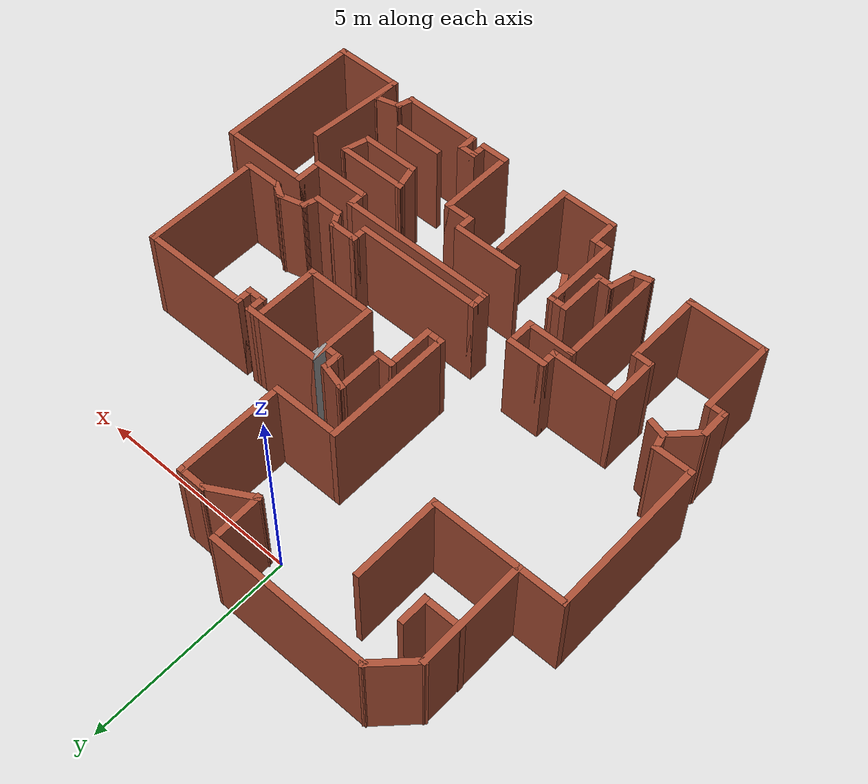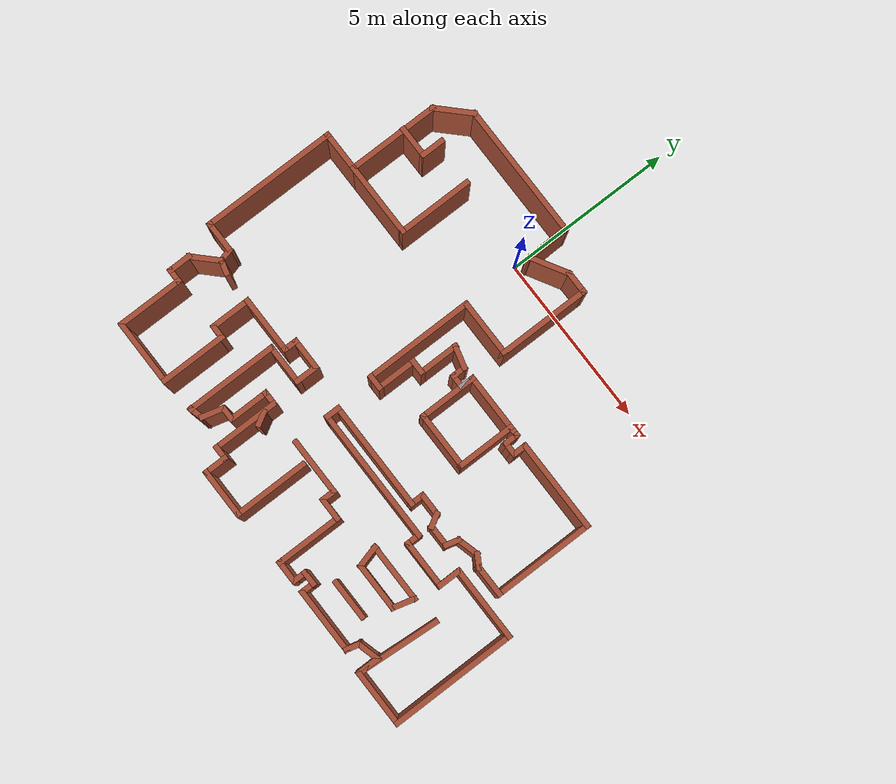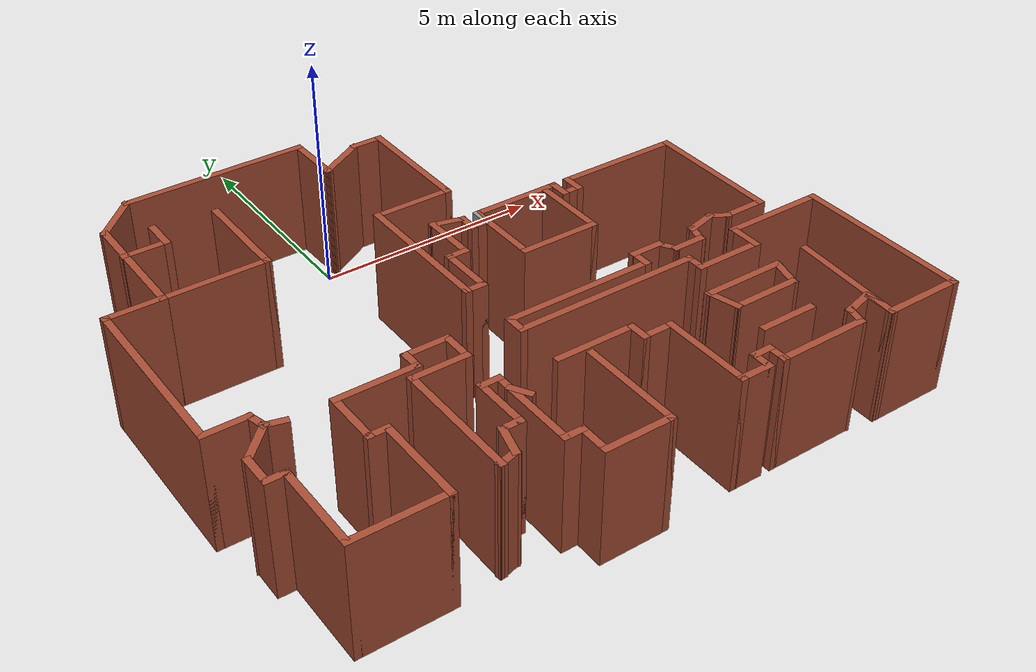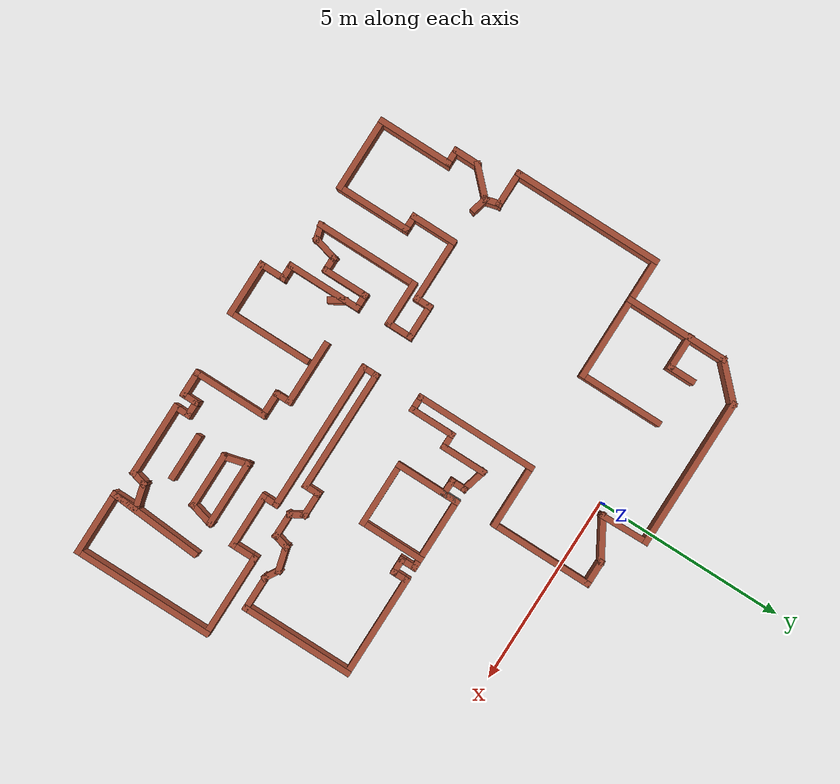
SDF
<?xml version='1.0'?>
<sdf version='1.6'>
  <model name='map_50'>
    <pose frame=''>1.05993 -4.24057 0 0 -0 0</pose>
    <link name='Wall_0'>
      <collision name='Wall_0_Collision'>
        <geometry>
          <box>
            <size>4 0.15 2.5</size>
          </box>
        </geometry>
        <pose frame=''>0 0 1.25 0 -0 0</pose>
      </collision>
      <visual name='Wall_0_Visual'>
        <pose frame=''>0 0 1.25 0 -0 0</pose>
        <geometry>
          <box>
            <size>4 0.15 2.5</size>
          </box>
        </geometry>
        <material>
          <script>
            <uri>file://media/materials/scripts/gazebo.material</uri>
            <name>Gazebo/Bricks</name>
          </script>
          <ambient>1 1 1 1</ambient>
        </material>
        <meta>
          <layer>0</layer>
        </meta>
      </visual>
      <pose frame=''>-2.76652 5.59051 0 0 -0 3.14159</pose>
    </link>
    <link name='Wall_1'>
      <collision name='Wall_1_Collision'>
        <geometry>
          <box>
            <size>1.25 0.15 2.5</size>
          </box>
        </geometry>
        <pose frame=''>0 0 1.25 0 -0 0</pose>
      </collision>
      <visual name='Wall_1_Visual'>
        <pose frame=''>0 0 1.25 0 -0 0</pose>
        <geometry>
          <box>
            <size>1.25 0.15 2.5</size>
          </box>
        </geometry>
        <material>
          <script>
            <uri>file://media/materials/scripts/gazebo.material</uri>
            <name>Gazebo/Bricks</name>
          </script>
          <ambient>1 1 1 1</ambient>
        </material>
        <meta>
          <layer>0</layer>
        </meta>
      </visual>
      <pose frame=''>-5.08043 5.2016 0 0 -0 -2.35619</pose>
    </link>
    <link name='Wall_10'>
      <collision name='Wall_10_Collision'>
        <geometry>
          <box>
            <size>4 0.15 2.5</size>
          </box>
        </geometry>
        <pose frame=''>0 0 1.25 0 -0 0</pose>
      </collision>
      <visual name='Wall_10_Visual'>
        <pose frame=''>0 0 1.25 0 -0 0</pose>
        <geometry>
          <box>
            <size>4 0.15 2.5</size>
          </box>
        </geometry>
        <material>
          <script>
            <uri>file://media/materials/scripts/gazebo.material</uri>
            <name>Gazebo/Bricks</name>
          </script>
          <ambient>1 1 1 1</ambient>
        </material>
        <meta>
          <layer>0</layer>
        </meta>
      </visual>
      <pose frame=''>-6.56934 0.28769 0 0 -0 -1.5708</pose>
    </link>
    <link name='Wall_100'>
      <collision name='Wall_100_Collision'>
        <geometry>
          <box>
            <size>1.33662 0.15 2.5</size>
          </box>
        </geometry>
        <pose frame=''>0 0 1.25 0 -0 0</pose>
      </collision>
      <visual name='Wall_100_Visual'>
        <pose frame=''>0 0 1.25 0 -0 0</pose>
        <geometry>
          <box>
            <size>1.33662 0.15 2.5</size>
          </box>
        </geometry>
        <material>
          <script>
            <uri>file://media/materials/scripts/gazebo.material</uri>
            <name>Gazebo/Bricks</name>
          </script>
          <ambient>1 1 1 1</ambient>
        </material>
        <meta>
          <layer>0</layer>
        </meta>
      </visual>
      <pose frame=''>-0.828058 4.99735 0 0 -0 1.59349</pose>
    </link>
    <link name='Wall_102'>
      <collision name='Wall_102_Collision'>
        <geometry>
          <box>
            <size>1.75 0.15 2.5</size>
          </box>
        </geometry>
        <pose frame=''>0 0 1.25 0 -0 0</pose>
      </collision>
      <visual name='Wall_102_Visual'>
        <pose frame=''>0 0 1.25 0 -0 0</pose>
        <geometry>
          <box>
            <size>1.75 0.15 2.5</size>
          </box>
        </geometry>
        <material>
          <script>
            <uri>file://media/materials/scripts/gazebo.material</uri>
            <name>Gazebo/Bricks</name>
          </script>
          <ambient>1 1 1 1</ambient>
        </material>
        <meta>
          <layer>0</layer>
        </meta>
      </visual>
      <pose frame=''>0.767588 0.498903 0 0 -0 -1.5708</pose>
    </link>
    <link name='Wall_103'>
      <collision name='Wall_103_Collision'>
        <geometry>
          <box>
            <size>1.75 0.15 2.5</size>
          </box>
        </geometry>
        <pose frame=''>0 0 1.25 0 -0 0</pose>
      </collision>
      <visual name='Wall_103_Visual'>
        <pose frame=''>0 0 1.25 0 -0 0</pose>
        <geometry>
          <box>
            <size>1.75 0.15 2.5</size>
          </box>
        </geometry>
        <material>
          <script>
            <uri>file://media/materials/scripts/gazebo.material</uri>
            <name>Gazebo/Bricks</name>
          </script>
          <ambient>1 1 1 1</ambient>
        </material>
        <meta>
          <layer>0</layer>
        </meta>
      </visual>
      <pose frame=''>1.56759 -0.301097 0 0 -0 0</pose>
    </link>
    <link name='Wall_105'>
      <collision name='Wall_105_Collision'>
        <geometry>
          <box>
            <size>1.75 0.15 2.5</size>
          </box>
        </geometry>
        <pose frame=''>0 0 1.25 0 -0 0</pose>
      </collision>
      <visual name='Wall_105_Visual'>
        <pose frame=''>0 0 1.25 0 -0 0</pose>
        <geometry>
          <box>
            <size>1.75 0.15 2.5</size>
          </box>
        </geometry>
        <material>
          <script>
            <uri>file://media/materials/scripts/gazebo.material</uri>
            <name>Gazebo/Bricks</name>
          </script>
          <ambient>1 1 1 1</ambient>
        </material>
        <meta>
          <layer>0</layer>
        </meta>
      </visual>
      <pose frame=''>2.36759 0.498903 0 0 -0 1.5708</pose>
    </link>
    <link name='Wall_107'>
      <collision name='Wall_107_Collision'>
        <geometry>
          <box>
            <size>2.49794 0.15 2.5</size>
          </box>
        </geometry>
        <pose frame=''>0 0 1.25 0 -0 0</pose>
      </collision>
      <visual name='Wall_107_Visual'>
        <pose frame=''>0 0 1.25 0 -0 0</pose>
        <geometry>
          <box>
            <size>2.49794 0.15 2.5</size>
          </box>
        </geometry>
        <material>
          <script>
            <uri>file://media/materials/scripts/gazebo.material</uri>
            <name>Gazebo/Bricks</name>
          </script>
          <ambient>1 1 1 1</ambient>
        </material>
        <meta>
          <layer>0</layer>
        </meta>
      </visual>
      <pose frame=''>5.0541 -4.44545 0 0 -0 -1.64306</pose>
    </link>
    <link name='Wall_109'>
      <collision name='Wall_109_Collision'>
        <geometry>
          <box>
            <size>0.5 0.15 2.5</size>
          </box>
        </geometry>
        <pose frame=''>0 0 1.25 0 -0 0</pose>
      </collision>
      <visual name='Wall_109_Visual'>
        <pose frame=''>0 0 1.25 0 -0 0</pose>
        <geometry>
          <box>
            <size>0.5 0.15 2.5</size>
          </box>
        </geometry>
        <material>
          <script>
            <uri>file://media/materials/scripts/gazebo.material</uri>
            <name>Gazebo/Bricks</name>
          </script>
          <ambient>1 1 1 1</ambient>
        </material>
        <meta>
          <layer>0</layer>
        </meta>
      </visual>
      <pose frame=''>-1.73903 -3.63717 0 0 -0 -1.0472</pose>
    </link>
    <link name='Wall_11'>
      <collision name='Wall_11_Collision'>
        <geometry>
          <box>
            <size>1 0.15 2.5</size>
          </box>
        </geometry>
        <pose frame=''>0 0 1.25 0 -0 0</pose>
      </collision>
      <visual name='Wall_11_Visual'>
        <pose frame=''>0 0 1.25 0 -0 0</pose>
        <geometry>
          <box>
            <size>1 0.15 2.5</size>
          </box>
        </geometry>
        <material>
          <script>
            <uri>file://media/materials/scripts/gazebo.material</uri>
            <name>Gazebo/Bricks</name>
          </script>
          <ambient>1 1 1 1</ambient>
        </material>
        <meta>
          <layer>0</layer>
        </meta>
      </visual>
      <pose frame=''>-6.14434 -1.63731 0 0 -0 0</pose>
    </link>
    <link name='Wall_111'>
      <collision name='Wall_111_Collision'>
        <geometry>
          <box>
            <size>0.5 0.15 2.5</size>
          </box>
        </geometry>
        <pose frame=''>0 0 1.25 0 -0 0</pose>
      </collision>
      <visual name='Wall_111_Visual'>
        <pose frame=''>0 0 1.25 0 -0 0</pose>
        <geometry>
          <box>
            <size>0.5 0.15 2.5</size>
          </box>
        </geometry>
        <material>
          <script>
            <uri>file://media/materials/scripts/gazebo.material</uri>
            <name>Gazebo/Bricks</name>
          </script>
          <ambient>1 1 1 1</ambient>
        </material>
        <meta>
          <layer>0</layer>
        </meta>
      </visual>
      <pose frame=''>-5.45971 -2.02068 0 0 -0 -0.261799</pose>
    </link>
    <link name='Wall_113'>
      <collision name='Wall_113_Collision'>
        <geometry>
          <box>
            <size>1.25 0.15 2.5</size>
          </box>
        </geometry>
        <pose frame=''>0 0 1.25 0 -0 0</pose>
      </collision>
      <visual name='Wall_113_Visual'>
        <pose frame=''>0 0 1.25 0 -0 0</pose>
        <geometry>
          <box>
            <size>1.25 0.15 2.5</size>
          </box>
        </geometry>
        <material>
          <script>
            <uri>file://media/materials/scripts/gazebo.material</uri>
            <name>Gazebo/Bricks</name>
          </script>
          <ambient>1 1 1 1</ambient>
        </material>
        <meta>
          <layer>0</layer>
        </meta>
      </visual>
      <pose frame=''>3.33189 -4.68169 0 0 -0 0</pose>
    </link>
    <link name='Wall_115'>
      <collision name='Wall_115_Collision'>
        <geometry>
          <box>
            <size>0.75 0.15 2.5</size>
          </box>
        </geometry>
        <pose frame=''>0 0 1.25 0 -0 0</pose>
      </collision>
      <visual name='Wall_115_Visual'>
        <pose frame=''>0 0 1.25 0 -0 0</pose>
        <geometry>
          <box>
            <size>0.75 0.15 2.5</size>
          </box>
        </geometry>
        <material>
          <script>
            <uri>file://media/materials/scripts/gazebo.material</uri>
            <name>Gazebo/Bricks</name>
          </script>
          <ambient>1 1 1 1</ambient>
        </material>
        <meta>
          <layer>0</layer>
        </meta>
      </visual>
      <pose frame=''>2.754 -3.63468 0 0 -0 -1.309</pose>
    </link>
    <link name='Wall_116'>
      <collision name='Wall_116_Collision'>
        <geometry>
          <box>
            <size>1.5 0.15 2.5</size>
          </box>
        </geometry>
        <pose frame=''>0 0 1.25 0 -0 0</pose>
      </collision>
      <visual name='Wall_116_Visual'>
        <pose frame=''>0 0 1.25 0 -0 0</pose>
        <geometry>
          <box>
            <size>1.5 0.15 2.5</size>
          </box>
        </geometry>
        <material>
          <script>
            <uri>file://media/materials/scripts/gazebo.material</uri>
            <name>Gazebo/Bricks</name>
          </script>
          <ambient>1 1 1 1</ambient>
        </material>
        <meta>
          <layer>0</layer>
        </meta>
      </visual>
      <pose frame=''>3.50665 -3.92445 0 0 -0 0</pose>
    </link>
    <link name='Wall_117'>
      <collision name='Wall_117_Collision'>
        <geometry>
          <box>
            <size>0.75 0.15 2.5</size>
          </box>
        </geometry>
        <pose frame=''>0 0 1.25 0 -0 0</pose>
      </collision>
      <visual name='Wall_117_Visual'>
        <pose frame=''>0 0 1.25 0 -0 0</pose>
        <geometry>
          <box>
            <size>0.75 0.15 2.5</size>
          </box>
        </geometry>
        <material>
          <script>
            <uri>file://media/materials/scripts/gazebo.material</uri>
            <name>Gazebo/Bricks</name>
          </script>
          <ambient>1 1 1 1</ambient>
        </material>
        <meta>
          <layer>0</layer>
        </meta>
      </visual>
      <pose frame=''>4.25929 -3.63468 0 0 -0 1.309</pose>
    </link>
    <link name='Wall_118'>
      <collision name='Wall_118_Collision'>
        <geometry>
          <box>
            <size>1.81058 0.15 2.5</size>
          </box>
        </geometry>
        <pose frame=''>0 0 1.25 0 -0 0</pose>
      </collision>
      <visual name='Wall_118_Visual'>
        <pose frame=''>0 0 1.25 0 -0 0</pose>
        <geometry>
          <box>
            <size>1.81058 0.15 2.5</size>
          </box>
        </geometry>
        <material>
          <script>
            <uri>file://media/materials/scripts/gazebo.material</uri>
            <name>Gazebo/Bricks</name>
          </script>
          <ambient>1 1 1 1</ambient>
        </material>
        <meta>
          <layer>0</layer>
        </meta>
      </visual>
      <pose frame=''>3.50665 -3.3449 0 0 -0 3.14159</pose>
    </link>
    <link name='Wall_12'>
      <collision name='Wall_12_Collision'>
        <geometry>
          <box>
            <size>0.5 0.15 2.5</size>
          </box>
        </geometry>
        <pose frame=''>0 0 1.25 0 -0 0</pose>
      </collision>
      <visual name='Wall_12_Visual'>
        <pose frame=''>0 0 1.25 0 -0 0</pose>
        <geometry>
          <box>
            <size>0.5 0.15 2.5</size>
          </box>
        </geometry>
        <material>
          <script>
            <uri>file://media/materials/scripts/gazebo.material</uri>
            <name>Gazebo/Bricks</name>
          </script>
          <ambient>1 1 1 1</ambient>
        </material>
        <meta>
          <layer>0</layer>
        </meta>
      </visual>
      <pose frame=''>-5.67404 -1.80635 0 0 -0 -1.309</pose>
    </link>
    <link name='Wall_13'>
      <collision name='Wall_13_Collision'>
        <geometry>
          <box>
            <size>1 0.15 2.5</size>
          </box>
        </geometry>
        <pose frame=''>0 0 1.25 0 -0 0</pose>
      </collision>
      <visual name='Wall_13_Visual'>
        <pose frame=''>0 0 1.25 0 -0 0</pose>
        <geometry>
          <box>
            <size>1 0.15 2.5</size>
          </box>
        </geometry>
        <material>
          <script>
            <uri>file://media/materials/scripts/gazebo.material</uri>
            <name>Gazebo/Bricks</name>
          </script>
          <ambient>1 1 1 1</ambient>
        </material>
        <meta>
          <layer>0</layer>
        </meta>
      </visual>
      <pose frame=''>-5.92927 -2.2759 0 0 -0 -2.35619</pose>
    </link>
    <link name='Wall_14'>
      <collision name='Wall_14_Collision'>
        <geometry>
          <box>
            <size>0.75 0.15 2.5</size>
          </box>
        </geometry>
        <pose frame=''>0 0 1.25 0 -0 0</pose>
      </collision>
      <visual name='Wall_14_Visual'>
        <pose frame=''>0 0 1.25 0 -0 0</pose>
        <geometry>
          <box>
            <size>0.75 0.15 2.5</size>
          </box>
        </geometry>
        <material>
          <script>
            <uri>file://media/materials/scripts/gazebo.material</uri>
            <name>Gazebo/Bricks</name>
          </script>
          <ambient>1 1 1 1</ambient>
        </material>
        <meta>
          <layer>0</layer>
        </meta>
      </visual>
      <pose frame=''>-6.22979 -2.87642 0 0 -0 -1.5708</pose>
    </link>
    <link name='Wall_15'>
      <collision name='Wall_15_Collision'>
        <geometry>
          <box>
            <size>0.5 0.15 2.5</size>
          </box>
        </geometry>
        <pose frame=''>0 0 1.25 0 -0 0</pose>
      </collision>
      <visual name='Wall_15_Visual'>
        <pose frame=''>0 0 1.25 0 -0 0</pose>
        <geometry>
          <box>
            <size>0.5 0.15 2.5</size>
          </box>
        </geometry>
        <material>
          <script>
            <uri>file://media/materials/scripts/gazebo.material</uri>
            <name>Gazebo/Bricks</name>
          </script>
          <ambient>1 1 1 1</ambient>
        </material>
        <meta>
          <layer>0</layer>
        </meta>
      </visual>
      <pose frame=''>-6.05479 -3.17643 0 0 -0 0</pose>
    </link>
    <link name='Wall_16'>
      <collision name='Wall_16_Collision'>
        <geometry>
          <box>
            <size>2 0.15 2.5</size>
          </box>
        </geometry>
        <pose frame=''>0 0 1.25 0 -0 0</pose>
      </collision>
      <visual name='Wall_16_Visual'>
        <pose frame=''>0 0 1.25 0 -0 0</pose>
        <geometry>
          <box>
            <size>2 0.15 2.5</size>
          </box>
        </geometry>
        <material>
          <script>
            <uri>file://media/materials/scripts/gazebo.material</uri>
            <name>Gazebo/Bricks</name>
          </script>
          <ambient>1 1 1 1</ambient>
        </material>
        <meta>
          <layer>0</layer>
        </meta>
      </visual>
      <pose frame=''>-5.87979 -4.10142 0 0 -0 -1.5708</pose>
    </link>
    <link name='Wall_17'>
      <collision name='Wall_17_Collision'>
        <geometry>
          <box>
            <size>2 0.15 2.5</size>
          </box>
        </geometry>
        <pose frame=''>0 0 1.25 0 -0 0</pose>
      </collision>
      <visual name='Wall_17_Visual'>
        <pose frame=''>0 0 1.25 0 -0 0</pose>
        <geometry>
          <box>
            <size>2 0.15 2.5</size>
          </box>
        </geometry>
        <material>
          <script>
            <uri>file://media/materials/scripts/gazebo.material</uri>
            <name>Gazebo/Bricks</name>
          </script>
          <ambient>1 1 1 1</ambient>
        </material>
        <meta>
          <layer>0</layer>
        </meta>
      </visual>
      <pose frame=''>-4.95479 -5.02642 0 0 -0 0</pose>
    </link>
    <link name='Wall_18'>
      <collision name='Wall_18_Collision'>
        <geometry>
          <box>
            <size>2 0.15 2.5</size>
          </box>
        </geometry>
        <pose frame=''>0 0 1.25 0 -0 0</pose>
      </collision>
      <visual name='Wall_18_Visual'>
        <pose frame=''>0 0 1.25 0 -0 0</pose>
        <geometry>
          <box>
            <size>2 0.15 2.5</size>
          </box>
        </geometry>
        <material>
          <script>
            <uri>file://media/materials/scripts/gazebo.material</uri>
            <name>Gazebo/Bricks</name>
          </script>
          <ambient>1 1 1 1</ambient>
        </material>
        <meta>
          <layer>0</layer>
        </meta>
      </visual>
      <pose frame=''>-4.02979 -4.10142 0 0 -0 1.5708</pose>
    </link>
    <link name='Wall_19'>
      <collision name='Wall_19_Collision'>
        <geometry>
          <box>
            <size>0.5 0.15 2.5</size>
          </box>
        </geometry>
        <pose frame=''>0 0 1.25 0 -0 0</pose>
      </collision>
      <visual name='Wall_19_Visual'>
        <pose frame=''>0 0 1.25 0 -0 0</pose>
        <geometry>
          <box>
            <size>0.5 0.15 2.5</size>
          </box>
        </geometry>
        <material>
          <script>
            <uri>file://media/materials/scripts/gazebo.material</uri>
            <name>Gazebo/Bricks</name>
          </script>
          <ambient>1 1 1 1</ambient>
        </material>
        <meta>
          <layer>0</layer>
        </meta>
      </visual>
      <pose frame=''>-4.20479 -3.17643 0 0 -0 3.14159</pose>
    </link>
    <link name='Wall_2'>
      <collision name='Wall_2_Collision'>
        <geometry>
          <box>
            <size>2.75 0.15 2.5</size>
          </box>
        </geometry>
        <pose frame=''>0 0 1.25 0 -0 0</pose>
      </collision>
      <visual name='Wall_2_Visual'>
        <pose frame=''>0 0 1.25 0 -0 0</pose>
        <geometry>
          <box>
            <size>2.75 0.15 2.5</size>
          </box>
        </geometry>
        <material>
          <script>
            <uri>file://media/materials/scripts/gazebo.material</uri>
            <name>Gazebo/Bricks</name>
          </script>
          <ambient>1 1 1 1</ambient>
        </material>
        <meta>
          <layer>0</layer>
        </meta>
      </visual>
      <pose frame=''>-5.46934 3.51269 0 0 -0 -1.5708</pose>
    </link>
    <link name='Wall_20'>
      <collision name='Wall_20_Collision'>
        <geometry>
          <box>
            <size>1.25 0.15 2.5</size>
          </box>
        </geometry>
        <pose frame=''>0 0 1.25 0 -0 0</pose>
      </collision>
      <visual name='Wall_20_Visual'>
        <pose frame=''>0 0 1.25 0 -0 0</pose>
        <geometry>
          <box>
            <size>1.25 0.15 2.5</size>
          </box>
        </geometry>
        <material>
          <script>
            <uri>file://media/materials/scripts/gazebo.material</uri>
            <name>Gazebo/Bricks</name>
          </script>
          <ambient>1 1 1 1</ambient>
        </material>
        <meta>
          <layer>0</layer>
        </meta>
      </visual>
      <pose frame=''>-4.37979 -2.62642 0 0 -0 1.5708</pose>
    </link>
    <link name='Wall_21'>
      <collision name='Wall_21_Collision'>
        <geometry>
          <box>
            <size>1.75 0.15 2.5</size>
          </box>
        </geometry>
        <pose frame=''>0 0 1.25 0 -0 0</pose>
      </collision>
      <visual name='Wall_21_Visual'>
        <pose frame=''>0 0 1.25 0 -0 0</pose>
        <geometry>
          <box>
            <size>1.75 0.15 2.5</size>
          </box>
        </geometry>
        <material>
          <script>
            <uri>file://media/materials/scripts/gazebo.material</uri>
            <name>Gazebo/Bricks</name>
          </script>
          <ambient>1 1 1 1</ambient>
        </material>
        <meta>
          <layer>0</layer>
        </meta>
      </visual>
      <pose frame=''>-3.57979 -2.07642 0 0 -0 0</pose>
    </link>
    <link name='Wall_22'>
      <collision name='Wall_22_Collision'>
        <geometry>
          <box>
            <size>0.5 0.15 2.5</size>
          </box>
        </geometry>
        <pose frame=''>0 0 1.25 0 -0 0</pose>
      </collision>
      <visual name='Wall_22_Visual'>
        <pose frame=''>0 0 1.25 0 -0 0</pose>
        <geometry>
          <box>
            <size>0.5 0.15 2.5</size>
          </box>
        </geometry>
        <material>
          <script>
            <uri>file://media/materials/scripts/gazebo.material</uri>
            <name>Gazebo/Bricks</name>
          </script>
          <ambient>1 1 1 1</ambient>
        </material>
        <meta>
          <layer>0</layer>
        </meta>
      </visual>
      <pose frame=''>-2.77979 -1.90142 0 0 -0 1.5708</pose>
    </link>
    <link name='Wall_23'>
      <collision name='Wall_23_Collision'>
        <geometry>
          <box>
            <size>1 0.15 2.5</size>
          </box>
        </geometry>
        <pose frame=''>0 0 1.25 0 -0 0</pose>
      </collision>
      <visual name='Wall_23_Visual'>
        <pose frame=''>0 0 1.25 0 -0 0</pose>
        <geometry>
          <box>
            <size>1 0.15 2.5</size>
          </box>
        </geometry>
        <material>
          <script>
            <uri>file://media/materials/scripts/gazebo.material</uri>
            <name>Gazebo/Bricks</name>
          </script>
          <ambient>1 1 1 1</ambient>
        </material>
        <meta>
          <layer>0</layer>
        </meta>
      </visual>
      <pose frame=''>-2.35479 -1.72642 0 0 -0 0</pose>
    </link>
    <link name='Wall_24'>
      <collision name='Wall_24_Collision'>
        <geometry>
          <box>
            <size>0.75 0.15 2.5</size>
          </box>
        </geometry>
        <pose frame=''>0 0 1.25 0 -0 0</pose>
      </collision>
      <visual name='Wall_24_Visual'>
        <pose frame=''>0 0 1.25 0 -0 0</pose>
        <geometry>
          <box>
            <size>0.75 0.15 2.5</size>
          </box>
        </geometry>
        <material>
          <script>
            <uri>file://media/materials/scripts/gazebo.material</uri>
            <name>Gazebo/Bricks</name>
          </script>
          <ambient>1 1 1 1</ambient>
        </material>
        <meta>
          <layer>0</layer>
        </meta>
      </visual>
      <pose frame=''>-1.92979 -2.02643 0 0 -0 -1.5708</pose>
    </link>
    <link name='Wall_25'>
      <collision name='Wall_25_Collision'>
        <geometry>
          <box>
            <size>1.25 0.15 2.5</size>
          </box>
        </geometry>
        <pose frame=''>0 0 1.25 0 -0 0</pose>
      </collision>
      <visual name='Wall_25_Visual'>
        <pose frame=''>0 0 1.25 0 -0 0</pose>
        <geometry>
          <box>
            <size>1.25 0.15 2.5</size>
          </box>
        </geometry>
        <material>
          <script>
            <uri>file://media/materials/scripts/gazebo.material</uri>
            <name>Gazebo/Bricks</name>
          </script>
          <ambient>1 1 1 1</ambient>
        </material>
        <meta>
          <layer>0</layer>
        </meta>
      </visual>
      <pose frame=''>-2.47979 -2.32642 0 0 -0 3.14159</pose>
    </link>
    <link name='Wall_26'>
      <collision name='Wall_26_Collision'>
        <geometry>
          <box>
            <size>2.75 0.15 2.5</size>
          </box>
        </geometry>
        <pose frame=''>0 0 1.25 0 -0 0</pose>
      </collision>
      <visual name='Wall_26_Visual'>
        <pose frame=''>0 0 1.25 0 -0 0</pose>
        <geometry>
          <box>
            <size>2.75 0.15 2.5</size>
          </box>
        </geometry>
        <material>
          <script>
            <uri>file://media/materials/scripts/gazebo.material</uri>
            <name>Gazebo/Bricks</name>
          </script>
          <ambient>1 1 1 1</ambient>
        </material>
        <meta>
          <layer>0</layer>
        </meta>
      </visual>
      <pose frame=''>-3.02979 -3.62642 0 0 -0 -1.5708</pose>
    </link>
    <link name='Wall_27'>
      <collision name='Wall_27_Collision'>
        <geometry>
          <box>
            <size>0.5 0.15 2.5</size>
          </box>
        </geometry>
        <pose frame=''>0 0 1.25 0 -0 0</pose>
      </collision>
      <visual name='Wall_27_Visual'>
        <pose frame=''>0 0 1.25 0 -0 0</pose>
        <geometry>
          <box>
            <size>0.5 0.15 2.5</size>
          </box>
        </geometry>
        <material>
          <script>
            <uri>file://media/materials/scripts/gazebo.material</uri>
            <name>Gazebo/Bricks</name>
          </script>
          <ambient>1 1 1 1</ambient>
        </material>
        <meta>
          <layer>0</layer>
        </meta>
      </visual>
      <pose frame=''>-2.86076 -4.88113 0 0 -0 0.261799</pose>
    </link>
    <link name='Wall_28'>
      <collision name='Wall_28_Collision'>
        <geometry>
          <box>
            <size>0.75 0.15 2.5</size>
          </box>
        </geometry>
        <pose frame=''>0 0 1.25 0 -0 0</pose>
      </collision>
      <visual name='Wall_28_Visual'>
        <pose frame=''>0 0 1.25 0 -0 0</pose>
        <geometry>
          <box>
            <size>0.75 0.15 2.5</size>
          </box>
        </geometry>
        <material>
          <script>
            <uri>file://media/materials/scripts/gazebo.material</uri>
            <name>Gazebo/Bricks</name>
          </script>
          <ambient>1 1 1 1</ambient>
        </material>
        <meta>
          <layer>0</layer>
        </meta>
      </visual>
      <pose frame=''>-2.61407 -4.54606 0 0 -0 1.309</pose>
    </link>
    <link name='Wall_3'>
      <collision name='Wall_3_Collision'>
        <geometry>
          <box>
            <size>2.25 0.15 2.5</size>
          </box>
        </geometry>
        <pose frame=''>0 0 1.25 0 -0 0</pose>
      </collision>
      <visual name='Wall_3_Visual'>
        <pose frame=''>0 0 1.25 0 -0 0</pose>
        <geometry>
          <box>
            <size>2.25 0.15 2.5</size>
          </box>
        </geometry>
        <material>
          <script>
            <uri>file://media/materials/scripts/gazebo.material</uri>
            <name>Gazebo/Bricks</name>
          </script>
          <ambient>1 1 1 1</ambient>
        </material>
        <meta>
          <layer>0</layer>
        </meta>
      </visual>
      <pose frame=''>-4.41934 2.21269 0 0 -0 0</pose>
    </link>
    <link name='Wall_33'>
      <collision name='Wall_33_Collision'>
        <geometry>
          <box>
            <size>0.5 0.15 2.5</size>
          </box>
        </geometry>
        <pose frame=''>0 0 1.25 0 -0 0</pose>
      </collision>
      <visual name='Wall_33_Visual'>
        <pose frame=''>0 0 1.25 0 -0 0</pose>
        <geometry>
          <box>
            <size>0.5 0.15 2.5</size>
          </box>
        </geometry>
        <material>
          <script>
            <uri>file://media/materials/scripts/gazebo.material</uri>
            <name>Gazebo/Bricks</name>
          </script>
          <ambient>1 1 1 1</ambient>
        </material>
        <meta>
          <layer>0</layer>
        </meta>
      </visual>
      <pose frame=''>-2.36143 -4.25628 0 0 -0 0</pose>
    </link>
    <link name='Wall_34'>
      <collision name='Wall_34_Collision'>
        <geometry>
          <box>
            <size>1.25 0.15 2.5</size>
          </box>
        </geometry>
        <pose frame=''>0 0 1.25 0 -0 0</pose>
      </collision>
      <visual name='Wall_34_Visual'>
        <pose frame=''>0 0 1.25 0 -0 0</pose>
        <geometry>
          <box>
            <size>1.25 0.15 2.5</size>
          </box>
        </geometry>
        <material>
          <script>
            <uri>file://media/materials/scripts/gazebo.material</uri>
            <name>Gazebo/Bricks</name>
          </script>
          <ambient>1 1 1 1</ambient>
        </material>
        <meta>
          <layer>0</layer>
        </meta>
      </visual>
      <pose frame=''>-2.18643 -3.70628 0 0 -0 1.5708</pose>
    </link>
    <link name='Wall_35'>
      <collision name='Wall_35_Collision'>
        <geometry>
          <box>
            <size>0.5 0.15 2.5</size>
          </box>
        </geometry>
        <pose frame=''>0 0 1.25 0 -0 0</pose>
      </collision>
      <visual name='Wall_35_Visual'>
        <pose frame=''>0 0 1.25 0 -0 0</pose>
        <geometry>
          <box>
            <size>0.5 0.15 2.5</size>
          </box>
        </geometry>
        <material>
          <script>
            <uri>file://media/materials/scripts/gazebo.material</uri>
            <name>Gazebo/Bricks</name>
          </script>
          <ambient>1 1 1 1</ambient>
        </material>
        <meta>
          <layer>0</layer>
        </meta>
      </visual>
      <pose frame=''>-2.01143 -3.15628 0 0 -0 0</pose>
    </link>
    <link name='Wall_36'>
      <collision name='Wall_36_Collision'>
        <geometry>
          <box>
            <size>2 0.15 2.5</size>
          </box>
        </geometry>
        <pose frame=''>0 0 1.25 0 -0 0</pose>
      </collision>
      <visual name='Wall_36_Visual'>
        <pose frame=''>0 0 1.25 0 -0 0</pose>
        <geometry>
          <box>
            <size>2 0.15 2.5</size>
          </box>
        </geometry>
        <material>
          <script>
            <uri>file://media/materials/scripts/gazebo.material</uri>
            <name>Gazebo/Bricks</name>
          </script>
          <ambient>1 1 1 1</ambient>
        </material>
        <meta>
          <layer>0</layer>
        </meta>
      </visual>
      <pose frame=''>-1.83643 -4.08128 0 0 -0 -1.5708</pose>
    </link>
    <link name='Wall_37'>
      <collision name='Wall_37_Collision'>
        <geometry>
          <box>
            <size>0.5 0.15 2.5</size>
          </box>
        </geometry>
        <pose frame=''>0 0 1.25 0 -0 0</pose>
      </collision>
      <visual name='Wall_37_Visual'>
        <pose frame=''>0 0 1.25 0 -0 0</pose>
        <geometry>
          <box>
            <size>0.5 0.15 2.5</size>
          </box>
        </geometry>
        <material>
          <script>
            <uri>file://media/materials/scripts/gazebo.material</uri>
            <name>Gazebo/Bricks</name>
          </script>
          <ambient>1 1 1 1</ambient>
        </material>
        <meta>
          <layer>0</layer>
        </meta>
      </visual>
      <pose frame=''>-1.66143 -5.00628 0 0 -0 0</pose>
    </link>
    <link name='Wall_38'>
      <collision name='Wall_38_Collision'>
        <geometry>
          <box>
            <size>0.75 0.15 2.5</size>
          </box>
        </geometry>
        <pose frame=''>0 0 1.25 0 -0 0</pose>
      </collision>
      <visual name='Wall_38_Visual'>
        <pose frame=''>0 0 1.25 0 -0 0</pose>
        <geometry>
          <box>
            <size>0.75 0.15 2.5</size>
          </box>
        </geometry>
        <material>
          <script>
            <uri>file://media/materials/scripts/gazebo.material</uri>
            <name>Gazebo/Bricks</name>
          </script>
          <ambient>1 1 1 1</ambient>
        </material>
        <meta>
          <layer>0</layer>
        </meta>
      </visual>
      <pose frame=''>-1.48643 -5.30628 0 0 -0 -1.5708</pose>
    </link>
    <link name='Wall_4'>
      <collision name='Wall_4_Collision'>
        <geometry>
          <box>
            <size>2.25 0.15 2.5</size>
          </box>
        </geometry>
        <pose frame=''>0 0 1.25 0 -0 0</pose>
      </collision>
      <visual name='Wall_4_Visual'>
        <pose frame=''>0 0 1.25 0 -0 0</pose>
        <geometry>
          <box>
            <size>2.25 0.15 2.5</size>
          </box>
        </geometry>
        <material>
          <script>
            <uri>file://media/materials/scripts/gazebo.material</uri>
            <name>Gazebo/Bricks</name>
          </script>
          <ambient>1 1 1 1</ambient>
        </material>
        <meta>
          <layer>0</layer>
        </meta>
      </visual>
      <pose frame=''>-3.36934 3.26269 0 0 -0 1.5708</pose>
    </link>
    <link name='Wall_41'>
      <collision name='Wall_41_Collision'>
        <geometry>
          <box>
            <size>1.5 0.15 2.5</size>
          </box>
        </geometry>
        <pose frame=''>0 0 1.25 0 -0 0</pose>
      </collision>
      <visual name='Wall_41_Visual'>
        <pose frame=''>0 0 1.25 0 -0 0</pose>
        <geometry>
          <box>
            <size>1.5 0.15 2.5</size>
          </box>
        </geometry>
        <material>
          <script>
            <uri>file://media/materials/scripts/gazebo.material</uri>
            <name>Gazebo/Bricks</name>
          </script>
          <ambient>1 1 1 1</ambient>
        </material>
        <meta>
          <layer>0</layer>
        </meta>
      </visual>
      <pose frame=''>-0.811426 -5.60628 0 0 -0 0</pose>
    </link>
    <link name='Wall_42'>
      <collision name='Wall_42_Collision'>
        <geometry>
          <box>
            <size>2.25 0.15 2.5</size>
          </box>
        </geometry>
        <pose frame=''>0 0 1.25 0 -0 0</pose>
      </collision>
      <visual name='Wall_42_Visual'>
        <pose frame=''>0 0 1.25 0 -0 0</pose>
        <geometry>
          <box>
            <size>2.25 0.15 2.5</size>
          </box>
        </geometry>
        <material>
          <script>
            <uri>file://media/materials/scripts/gazebo.material</uri>
            <name>Gazebo/Bricks</name>
          </script>
          <ambient>1 1 1 1</ambient>
        </material>
        <meta>
          <layer>0</layer>
        </meta>
      </visual>
      <pose frame=''>-0.136426 -4.55628 0 0 -0 1.5708</pose>
    </link>
    <link name='Wall_44'>
      <collision name='Wall_44_Collision'>
        <geometry>
          <box>
            <size>1.75 0.15 2.5</size>
          </box>
        </geometry>
        <pose frame=''>0 0 1.25 0 -0 0</pose>
      </collision>
      <visual name='Wall_44_Visual'>
        <pose frame=''>0 0 1.25 0 -0 0</pose>
        <geometry>
          <box>
            <size>1.75 0.15 2.5</size>
          </box>
        </geometry>
        <material>
          <script>
            <uri>file://media/materials/scripts/gazebo.material</uri>
            <name>Gazebo/Bricks</name>
          </script>
          <ambient>1 1 1 1</ambient>
        </material>
        <meta>
          <layer>0</layer>
        </meta>
      </visual>
      <pose frame=''>0.099195 -3.30972 0 0 -0 0</pose>
    </link>
    <link name='Wall_45'>
      <collision name='Wall_45_Collision'>
        <geometry>
          <box>
            <size>0.5 0.15 2.5</size>
          </box>
        </geometry>
        <pose frame=''>0 0 1.25 0 -0 0</pose>
      </collision>
      <visual name='Wall_45_Visual'>
        <pose frame=''>0 0 1.25 0 -0 0</pose>
        <geometry>
          <box>
            <size>0.5 0.15 2.5</size>
          </box>
        </geometry>
        <material>
          <script>
            <uri>file://media/materials/scripts/gazebo.material</uri>
            <name>Gazebo/Bricks</name>
          </script>
          <ambient>1 1 1 1</ambient>
        </material>
        <meta>
          <layer>0</layer>
        </meta>
      </visual>
      <pose frame=''>0.899195 -3.48472 0 0 -0 -1.5708</pose>
    </link>
    <link name='Wall_46'>
      <collision name='Wall_46_Collision'>
        <geometry>
          <box>
            <size>0.75 0.15 2.5</size>
          </box>
        </geometry>
        <pose frame=''>0 0 1.25 0 -0 0</pose>
      </collision>
      <visual name='Wall_46_Visual'>
        <pose frame=''>0 0 1.25 0 -0 0</pose>
        <geometry>
          <box>
            <size>0.75 0.15 2.5</size>
          </box>
        </geometry>
        <material>
          <script>
            <uri>file://media/materials/scripts/gazebo.material</uri>
            <name>Gazebo/Bricks</name>
          </script>
          <ambient>1 1 1 1</ambient>
        </material>
        <meta>
          <layer>0</layer>
        </meta>
      </visual>
      <pose frame=''>1.1992 -3.65972 0 0 -0 0</pose>
    </link>
    <link name='Wall_47'>
      <collision name='Wall_47_Collision'>
        <geometry>
          <box>
            <size>2 0.15 2.5</size>
          </box>
        </geometry>
        <pose frame=''>0 0 1.25 0 -0 0</pose>
      </collision>
      <visual name='Wall_47_Visual'>
        <pose frame=''>0 0 1.25 0 -0 0</pose>
        <geometry>
          <box>
            <size>2 0.15 2.5</size>
          </box>
        </geometry>
        <material>
          <script>
            <uri>file://media/materials/scripts/gazebo.material</uri>
            <name>Gazebo/Bricks</name>
          </script>
          <ambient>1 1 1 1</ambient>
        </material>
        <meta>
          <layer>0</layer>
        </meta>
      </visual>
      <pose frame=''>1.4992 -4.58472 0 0 -0 -1.5708</pose>
    </link>
    <link name='Wall_48'>
      <collision name='Wall_48_Collision'>
        <geometry>
          <box>
            <size>0.75 0.15 2.5</size>
          </box>
        </geometry>
        <pose frame=''>0 0 1.25 0 -0 0</pose>
      </collision>
      <visual name='Wall_48_Visual'>
        <pose frame=''>0 0 1.25 0 -0 0</pose>
        <geometry>
          <box>
            <size>0.75 0.15 2.5</size>
          </box>
        </geometry>
        <material>
          <script>
            <uri>file://media/materials/scripts/gazebo.material</uri>
            <name>Gazebo/Bricks</name>
          </script>
          <ambient>1 1 1 1</ambient>
        </material>
        <meta>
          <layer>0</layer>
        </meta>
      </visual>
      <pose frame=''>1.7992 -5.50972 0 0 -0 0</pose>
    </link>
    <link name='Wall_49'>
      <collision name='Wall_49_Collision'>
        <geometry>
          <box>
            <size>0.5 0.15 2.5</size>
          </box>
        </geometry>
        <pose frame=''>0 0 1.25 0 -0 0</pose>
      </collision>
      <visual name='Wall_49_Visual'>
        <pose frame=''>0 0 1.25 0 -0 0</pose>
        <geometry>
          <box>
            <size>0.5 0.15 2.5</size>
          </box>
        </geometry>
        <material>
          <script>
            <uri>file://media/materials/scripts/gazebo.material</uri>
            <name>Gazebo/Bricks</name>
          </script>
          <ambient>1 1 1 1</ambient>
        </material>
        <meta>
          <layer>0</layer>
        </meta>
      </visual>
      <pose frame=''>2.09919 -5.33472 0 0 -0 1.5708</pose>
    </link>
    <link name='Wall_50'>
      <collision name='Wall_50_Collision'>
        <geometry>
          <box>
            <size>0.5 0.15 2.5</size>
          </box>
        </geometry>
        <pose frame=''>0 0 1.25 0 -0 0</pose>
      </collision>
      <visual name='Wall_50_Visual'>
        <pose frame=''>0 0 1.25 0 -0 0</pose>
        <geometry>
          <box>
            <size>0.5 0.15 2.5</size>
          </box>
        </geometry>
        <material>
          <script>
            <uri>file://media/materials/scripts/gazebo.material</uri>
            <name>Gazebo/Bricks</name>
          </script>
          <ambient>1 1 1 1</ambient>
        </material>
        <meta>
          <layer>0</layer>
        </meta>
      </visual>
      <pose frame=''>2.2742 -5.15972 0 0 -0 0</pose>
    </link>
    <link name='Wall_51'>
      <collision name='Wall_51_Collision'>
        <geometry>
          <box>
            <size>0.5 0.15 2.5</size>
          </box>
        </geometry>
        <pose frame=''>0 0 1.25 0 -0 0</pose>
      </collision>
      <visual name='Wall_51_Visual'>
        <pose frame=''>0 0 1.25 0 -0 0</pose>
        <geometry>
          <box>
            <size>0.5 0.15 2.5</size>
          </box>
        </geometry>
        <material>
          <script>
            <uri>file://media/materials/scripts/gazebo.material</uri>
            <name>Gazebo/Bricks</name>
          </script>
          <ambient>1 1 1 1</ambient>
        </material>
        <meta>
          <layer>0</layer>
        </meta>
      </visual>
      <pose frame=''>2.4492 -5.33472 0 0 -0 -1.5708</pose>
    </link>
    <link name='Wall_52'>
      <collision name='Wall_52_Collision'>
        <geometry>
          <box>
            <size>2 0.15 2.5</size>
          </box>
        </geometry>
        <pose frame=''>0 0 1.25 0 -0 0</pose>
      </collision>
      <visual name='Wall_52_Visual'>
        <pose frame=''>0 0 1.25 0 -0 0</pose>
        <geometry>
          <box>
            <size>2 0.15 2.5</size>
          </box>
        </geometry>
        <material>
          <script>
            <uri>file://media/materials/scripts/gazebo.material</uri>
            <name>Gazebo/Bricks</name>
          </script>
          <ambient>1 1 1 1</ambient>
        </material>
        <meta>
          <layer>0</layer>
        </meta>
      </visual>
      <pose frame=''>3.37419 -5.50972 0 0 -0 0</pose>
    </link>
    <link name='Wall_53'>
      <collision name='Wall_53_Collision'>
        <geometry>
          <box>
            <size>0.5 0.15 2.5</size>
          </box>
        </geometry>
        <pose frame=''>0 0 1.25 0 -0 0</pose>
      </collision>
      <visual name='Wall_53_Visual'>
        <pose frame=''>0 0 1.25 0 -0 0</pose>
        <geometry>
          <box>
            <size>0.5 0.15 2.5</size>
          </box>
        </geometry>
        <material>
          <script>
            <uri>file://media/materials/scripts/gazebo.material</uri>
            <name>Gazebo/Bricks</name>
          </script>
          <ambient>1 1 1 1</ambient>
        </material>
        <meta>
          <layer>0</layer>
        </meta>
      </visual>
      <pose frame=''>4.34449 -5.34068 0 0 -0 1.309</pose>
    </link>
    <link name='Wall_54'>
      <collision name='Wall_54_Collision'>
        <geometry>
          <box>
            <size>0.75 0.15 2.5</size>
          </box>
        </geometry>
        <pose frame=''>0 0 1.25 0 -0 0</pose>
      </collision>
      <visual name='Wall_54_Visual'>
        <pose frame=''>0 0 1.25 0 -0 0</pose>
        <geometry>
          <box>
            <size>0.75 0.15 2.5</size>
          </box>
        </geometry>
        <material>
          <script>
            <uri>file://media/materials/scripts/gazebo.material</uri>
            <name>Gazebo/Bricks</name>
          </script>
          <ambient>1 1 1 1</ambient>
        </material>
        <meta>
          <layer>0</layer>
        </meta>
      </visual>
      <pose frame=''>4.67956 -5.094 0 0 -0 0.261799</pose>
    </link>
    <link name='Wall_55'>
      <collision name='Wall_55_Collision'>
        <geometry>
          <box>
            <size>0.75 0.15 2.5</size>
          </box>
        </geometry>
        <pose frame=''>0 0 1.25 0 -0 0</pose>
      </collision>
      <visual name='Wall_55_Visual'>
        <pose frame=''>0 0 1.25 0 -0 0</pose>
        <geometry>
          <box>
            <size>0.75 0.15 2.5</size>
          </box>
        </geometry>
        <material>
          <script>
            <uri>file://media/materials/scripts/gazebo.material</uri>
            <name>Gazebo/Bricks</name>
          </script>
          <ambient>1 1 1 1</ambient>
        </material>
        <meta>
          <layer>0</layer>
        </meta>
      </visual>
      <pose frame=''>4.96934 -5.31635 0 0 -0 -1.5708</pose>
    </link>
    <link name='Wall_56'>
      <collision name='Wall_56_Collision'>
        <geometry>
          <box>
            <size>1.75 0.15 2.5</size>
          </box>
        </geometry>
        <pose frame=''>0 0 1.25 0 -0 0</pose>
      </collision>
      <visual name='Wall_56_Visual'>
        <pose frame=''>0 0 1.25 0 -0 0</pose>
        <geometry>
          <box>
            <size>1.75 0.15 2.5</size>
          </box>
        </geometry>
        <material>
          <script>
            <uri>file://media/materials/scripts/gazebo.material</uri>
            <name>Gazebo/Bricks</name>
          </script>
          <ambient>1 1 1 1</ambient>
        </material>
        <meta>
          <layer>0</layer>
        </meta>
      </visual>
      <pose frame=''>5.76934 -5.61635 0 0 -0 0</pose>
    </link>
    <link name='Wall_57'>
      <collision name='Wall_57_Collision'>
        <geometry>
          <box>
            <size>3.75 0.15 2.5</size>
          </box>
        </geometry>
        <pose frame=''>0 0 1.25 0 -0 0</pose>
      </collision>
      <visual name='Wall_57_Visual'>
        <pose frame=''>0 0 1.25 0 -0 0</pose>
        <geometry>
          <box>
            <size>3.75 0.15 2.5</size>
          </box>
        </geometry>
        <material>
          <script>
            <uri>file://media/materials/scripts/gazebo.material</uri>
            <name>Gazebo/Bricks</name>
          </script>
          <ambient>1 1 1 1</ambient>
        </material>
        <meta>
          <layer>0</layer>
        </meta>
      </visual>
      <pose frame=''>6.56934 -3.81635 0 0 -0 1.5708</pose>
    </link>
    <link name='Wall_58'>
      <collision name='Wall_58_Collision'>
        <geometry>
          <box>
            <size>2.25 0.15 2.5</size>
          </box>
        </geometry>
        <pose frame=''>0 0 1.25 0 -0 0</pose>
      </collision>
      <visual name='Wall_58_Visual'>
        <pose frame=''>0 0 1.25 0 -0 0</pose>
        <geometry>
          <box>
            <size>2.25 0.15 2.5</size>
          </box>
        </geometry>
        <material>
          <script>
            <uri>file://media/materials/scripts/gazebo.material</uri>
            <name>Gazebo/Bricks</name>
          </script>
          <ambient>1 1 1 1</ambient>
        </material>
        <meta>
          <layer>0</layer>
        </meta>
      </visual>
      <pose frame=''>5.51934 -2.01635 0 0 -0 3.14159</pose>
    </link>
    <link name='Wall_59'>
      <collision name='Wall_59_Collision'>
        <geometry>
          <box>
            <size>0.75 0.15 2.5</size>
          </box>
        </geometry>
        <pose frame=''>0 0 1.25 0 -0 0</pose>
      </collision>
      <visual name='Wall_59_Visual'>
        <pose frame=''>0 0 1.25 0 -0 0</pose>
        <geometry>
          <box>
            <size>0.75 0.15 2.5</size>
          </box>
        </geometry>
        <material>
          <script>
            <uri>file://media/materials/scripts/gazebo.material</uri>
            <name>Gazebo/Bricks</name>
          </script>
          <ambient>1 1 1 1</ambient>
        </material>
        <meta>
          <layer>0</layer>
        </meta>
      </visual>
      <pose frame=''>4.46934 -2.31635 0 0 -0 -1.5708</pose>
    </link>
    <link name='Wall_6'>
      <collision name='Wall_6_Collision'>
        <geometry>
          <box>
            <size>1 0.15 2.5</size>
          </box>
        </geometry>
        <pose frame=''>0 0 1.25 0 -0 0</pose>
      </collision>
      <visual name='Wall_6_Visual'>
        <pose frame=''>0 0 1.25 0 -0 0</pose>
        <geometry>
          <box>
            <size>1 0.15 2.5</size>
          </box>
        </geometry>
        <material>
          <script>
            <uri>file://media/materials/scripts/gazebo.material</uri>
            <name>Gazebo/Bricks</name>
          </script>
          <ambient>1 1 1 1</ambient>
        </material>
        <meta>
          <layer>0</layer>
        </meta>
      </visual>
      <pose frame=''>-5.06012 3.86675 0 0 -0 0</pose>
    </link>
    <link name='Wall_60'>
      <collision name='Wall_60_Collision'>
        <geometry>
          <box>
            <size>1.5 0.15 2.5</size>
          </box>
        </geometry>
        <pose frame=''>0 0 1.25 0 -0 0</pose>
      </collision>
      <visual name='Wall_60_Visual'>
        <pose frame=''>0 0 1.25 0 -0 0</pose>
        <geometry>
          <box>
            <size>1.5 0.15 2.5</size>
          </box>
        </geometry>
        <material>
          <script>
            <uri>file://media/materials/scripts/gazebo.material</uri>
            <name>Gazebo/Bricks</name>
          </script>
          <ambient>1 1 1 1</ambient>
        </material>
        <meta>
          <layer>0</layer>
        </meta>
      </visual>
      <pose frame=''>3.79434 -2.61635 0 0 -0 3.14159</pose>
    </link>
    <link name='Wall_61'>
      <collision name='Wall_61_Collision'>
        <geometry>
          <box>
            <size>0.5 0.15 2.5</size>
          </box>
        </geometry>
        <pose frame=''>0 0 1.25 0 -0 0</pose>
      </collision>
      <visual name='Wall_61_Visual'>
        <pose frame=''>0 0 1.25 0 -0 0</pose>
        <geometry>
          <box>
            <size>0.5 0.15 2.5</size>
          </box>
        </geometry>
        <material>
          <script>
            <uri>file://media/materials/scripts/gazebo.material</uri>
            <name>Gazebo/Bricks</name>
          </script>
          <ambient>1 1 1 1</ambient>
        </material>
        <meta>
          <layer>0</layer>
        </meta>
      </visual>
      <pose frame=''>3.11934 -2.44135 0 0 -0 1.5708</pose>
    </link>
    <link name='Wall_62'>
      <collision name='Wall_62_Collision'>
        <geometry>
          <box>
            <size>4 0.15 2.5</size>
          </box>
        </geometry>
        <pose frame=''>0 0 1.25 0 -0 0</pose>
      </collision>
      <visual name='Wall_62_Visual'>
        <pose frame=''>0 0 1.25 0 -0 0</pose>
        <geometry>
          <box>
            <size>4 0.15 2.5</size>
          </box>
        </geometry>
        <material>
          <script>
            <uri>file://media/materials/scripts/gazebo.material</uri>
            <name>Gazebo/Bricks</name>
          </script>
          <ambient>1 1 1 1</ambient>
        </material>
        <meta>
          <layer>0</layer>
        </meta>
      </visual>
      <pose frame=''>1.19434 -2.26635 0 0 -0 3.14159</pose>
    </link>
    <link name='Wall_63'>
      <collision name='Wall_63_Collision'>
        <geometry>
          <box>
            <size>0.5 0.15 2.5</size>
          </box>
        </geometry>
        <pose frame=''>0 0 1.25 0 -0 0</pose>
      </collision>
      <visual name='Wall_63_Visual'>
        <pose frame=''>0 0 1.25 0 -0 0</pose>
        <geometry>
          <box>
            <size>0.5 0.15 2.5</size>
          </box>
        </geometry>
        <material>
          <script>
            <uri>file://media/materials/scripts/gazebo.material</uri>
            <name>Gazebo/Bricks</name>
          </script>
          <ambient>1 1 1 1</ambient>
        </material>
        <meta>
          <layer>0</layer>
        </meta>
      </visual>
      <pose frame=''>-0.730663 -2.09135 0 0 -0 1.5708</pose>
    </link>
    <link name='Wall_7'>
      <collision name='Wall_7_Collision'>
        <geometry>
          <box>
            <size>0.75 0.15 2.5</size>
          </box>
        </geometry>
        <pose frame=''>0 0 1.25 0 -0 0</pose>
      </collision>
      <visual name='Wall_7_Visual'>
        <pose frame=''>0 0 1.25 0 -0 0</pose>
        <geometry>
          <box>
            <size>0.75 0.15 2.5</size>
          </box>
        </geometry>
        <material>
          <script>
            <uri>file://media/materials/scripts/gazebo.material</uri>
            <name>Gazebo/Bricks</name>
          </script>
          <ambient>1 1 1 1</ambient>
        </material>
        <meta>
          <layer>0</layer>
        </meta>
      </visual>
      <pose frame=''>-4.63512 4.16675 0 0 -0 1.5708</pose>
    </link>
    <link name='Wall_70'>
      <collision name='Wall_70_Collision'>
        <geometry>
          <box>
            <size>3.25 0.15 2.5</size>
          </box>
        </geometry>
        <pose frame=''>0 0 1.25 0 -0 0</pose>
      </collision>
      <visual name='Wall_70_Visual'>
        <pose frame=''>0 0 1.25 0 -0 0</pose>
        <geometry>
          <box>
            <size>3.25 0.15 2.5</size>
          </box>
        </geometry>
        <material>
          <script>
            <uri>file://media/materials/scripts/gazebo.material</uri>
            <name>Gazebo/Bricks</name>
          </script>
          <ambient>1 1 1 1</ambient>
        </material>
        <meta>
          <layer>0</layer>
        </meta>
      </visual>
      <pose frame=''>0.819337 -1.91635 0 0 -0 0</pose>
    </link>
    <link name='Wall_71'>
      <collision name='Wall_71_Collision'>
        <geometry>
          <box>
            <size>0.5 0.15 2.5</size>
          </box>
        </geometry>
        <pose frame=''>0 0 1.25 0 -0 0</pose>
      </collision>
      <visual name='Wall_71_Visual'>
        <pose frame=''>0 0 1.25 0 -0 0</pose>
        <geometry>
          <box>
            <size>0.5 0.15 2.5</size>
          </box>
        </geometry>
        <material>
          <script>
            <uri>file://media/materials/scripts/gazebo.material</uri>
            <name>Gazebo/Bricks</name>
          </script>
          <ambient>1 1 1 1</ambient>
        </material>
        <meta>
          <layer>0</layer>
        </meta>
      </visual>
      <pose frame=''>2.36934 -1.74135 0 0 -0 1.5708</pose>
    </link>
    <link name='Wall_74'>
      <collision name='Wall_74_Collision'>
        <geometry>
          <box>
            <size>0.75 0.15 2.5</size>
          </box>
        </geometry>
        <pose frame=''>0 0 1.25 0 -0 0</pose>
      </collision>
      <visual name='Wall_74_Visual'>
        <pose frame=''>0 0 1.25 0 -0 0</pose>
        <geometry>
          <box>
            <size>0.75 0.15 2.5</size>
          </box>
        </geometry>
        <material>
          <script>
            <uri>file://media/materials/scripts/gazebo.material</uri>
            <name>Gazebo/Bricks</name>
          </script>
          <ambient>1 1 1 1</ambient>
        </material>
        <meta>
          <layer>0</layer>
        </meta>
      </visual>
      <pose frame=''>2.66934 -1.56635 0 0 -0 0</pose>
    </link>
    <link name='Wall_75'>
      <collision name='Wall_75_Collision'>
        <geometry>
          <box>
            <size>0.5 0.15 2.5</size>
          </box>
        </geometry>
        <pose frame=''>0 0 1.25 0 -0 0</pose>
      </collision>
      <visual name='Wall_75_Visual'>
        <pose frame=''>0 0 1.25 0 -0 0</pose>
        <geometry>
          <box>
            <size>0.5 0.15 2.5</size>
          </box>
        </geometry>
        <material>
          <script>
            <uri>file://media/materials/scripts/gazebo.material</uri>
            <name>Gazebo/Bricks</name>
          </script>
          <ambient>1 1 1 1</ambient>
        </material>
        <meta>
          <layer>0</layer>
        </meta>
      </visual>
      <pose frame=''>3.05684 -1.71791 0 0 -0 -1.0472</pose>
    </link>
    <link name='Wall_76'>
      <collision name='Wall_76_Collision'>
        <geometry>
          <box>
            <size>0.75 0.15 2.5</size>
          </box>
        </geometry>
        <pose frame=''>0 0 1.25 0 -0 0</pose>
      </collision>
      <visual name='Wall_76_Visual'>
        <pose frame=''>0 0 1.25 0 -0 0</pose>
        <geometry>
          <box>
            <size>0.75 0.15 2.5</size>
          </box>
        </geometry>
        <material>
          <script>
            <uri>file://media/materials/scripts/gazebo.material</uri>
            <name>Gazebo/Bricks</name>
          </script>
          <ambient>1 1 1 1</ambient>
        </material>
        <meta>
          <layer>0</layer>
        </meta>
      </visual>
      <pose frame=''>3.44434 -1.86946 0 0 -0 0</pose>
    </link>
    <link name='Wall_77'>
      <collision name='Wall_77_Collision'>
        <geometry>
          <box>
            <size>0.5 0.15 2.5</size>
          </box>
        </geometry>
        <pose frame=''>0 0 1.25 0 -0 0</pose>
      </collision>
      <visual name='Wall_77_Visual'>
        <pose frame=''>0 0 1.25 0 -0 0</pose>
        <geometry>
          <box>
            <size>0.5 0.15 2.5</size>
          </box>
        </geometry>
        <material>
          <script>
            <uri>file://media/materials/scripts/gazebo.material</uri>
            <name>Gazebo/Bricks</name>
          </script>
          <ambient>1 1 1 1</ambient>
        </material>
        <meta>
          <layer>0</layer>
        </meta>
      </visual>
      <pose frame=''>3.78963 -1.70043 0 0 -0 1.309</pose>
    </link>
    <link name='Wall_78'>
      <collision name='Wall_78_Collision'>
        <geometry>
          <box>
            <size>0.75 0.15 2.5</size>
          </box>
        </geometry>
        <pose frame=''>0 0 1.25 0 -0 0</pose>
      </collision>
      <visual name='Wall_78_Visual'>
        <pose frame=''>0 0 1.25 0 -0 0</pose>
        <geometry>
          <box>
            <size>0.75 0.15 2.5</size>
          </box>
        </geometry>
        <material>
          <script>
            <uri>file://media/materials/scripts/gazebo.material</uri>
            <name>Gazebo/Bricks</name>
          </script>
          <ambient>1 1 1 1</ambient>
        </material>
        <meta>
          <layer>0</layer>
        </meta>
      </visual>
      <pose frame=''>4.1247 -1.45374 0 0 -0 0.261799</pose>
    </link>
    <link name='Wall_79'>
      <collision name='Wall_79_Collision'>
        <geometry>
          <box>
            <size>0.5 0.15 2.5</size>
          </box>
        </geometry>
        <pose frame=''>0 0 1.25 0 -0 0</pose>
      </collision>
      <visual name='Wall_79_Visual'>
        <pose frame=''>0 0 1.25 0 -0 0</pose>
        <geometry>
          <box>
            <size>0.5 0.15 2.5</size>
          </box>
        </geometry>
        <material>
          <script>
            <uri>file://media/materials/scripts/gazebo.material</uri>
            <name>Gazebo/Bricks</name>
          </script>
          <ambient>1 1 1 1</ambient>
        </material>
        <meta>
          <layer>0</layer>
        </meta>
      </visual>
      <pose frame=''>4.56603 -1.4636 0 0 -0 -0.523599</pose>
    </link>
    <link name='Wall_80'>
      <collision name='Wall_80_Collision'>
        <geometry>
          <box>
            <size>1 0.15 2.5</size>
          </box>
        </geometry>
        <pose frame=''>0 0 1.25 0 -0 0</pose>
      </collision>
      <visual name='Wall_80_Visual'>
        <pose frame=''>0 0 1.25 0 -0 0</pose>
        <geometry>
          <box>
            <size>1 0.15 2.5</size>
          </box>
        </geometry>
        <material>
          <script>
            <uri>file://media/materials/scripts/gazebo.material</uri>
            <name>Gazebo/Bricks</name>
          </script>
          <ambient>1 1 1 1</ambient>
        </material>
        <meta>
          <layer>0</layer>
        </meta>
      </visual>
      <pose frame=''>5.14259 -1.5511 0 0 -0 0</pose>
    </link>
    <link name='Wall_81'>
      <collision name='Wall_81_Collision'>
        <geometry>
          <box>
            <size>3 0.15 2.5</size>
          </box>
        </geometry>
        <pose frame=''>0 0 1.25 0 -0 0</pose>
      </collision>
      <visual name='Wall_81_Visual'>
        <pose frame=''>0 0 1.25 0 -0 0</pose>
        <geometry>
          <box>
            <size>3 0.15 2.5</size>
          </box>
        </geometry>
        <material>
          <script>
            <uri>file://media/materials/scripts/gazebo.material</uri>
            <name>Gazebo/Bricks</name>
          </script>
          <ambient>1 1 1 1</ambient>
        </material>
        <meta>
          <layer>0</layer>
        </meta>
      </visual>
      <pose frame=''>5.56759 -0.126097 0 0 -0 1.5708</pose>
    </link>
    <link name='Wall_82'>
      <collision name='Wall_82_Collision'>
        <geometry>
          <box>
            <size>2.75 0.15 2.5</size>
          </box>
        </geometry>
        <pose frame=''>0 0 1.25 0 -0 0</pose>
      </collision>
      <visual name='Wall_82_Visual'>
        <pose frame=''>0 0 1.25 0 -0 0</pose>
        <geometry>
          <box>
            <size>2.75 0.15 2.5</size>
          </box>
        </geometry>
        <material>
          <script>
            <uri>file://media/materials/scripts/gazebo.material</uri>
            <name>Gazebo/Bricks</name>
          </script>
          <ambient>1 1 1 1</ambient>
        </material>
        <meta>
          <layer>0</layer>
        </meta>
      </visual>
      <pose frame=''>4.26759 1.2989 0 0 -0 3.14159</pose>
    </link>
    <link name='Wall_83'>
      <collision name='Wall_83_Collision'>
        <geometry>
          <box>
            <size>0.5 0.15 2.5</size>
          </box>
        </geometry>
        <pose frame=''>0 0 1.25 0 -0 0</pose>
      </collision>
      <visual name='Wall_83_Visual'>
        <pose frame=''>0 0 1.25 0 -0 0</pose>
        <geometry>
          <box>
            <size>0.5 0.15 2.5</size>
          </box>
        </geometry>
        <material>
          <script>
            <uri>file://media/materials/scripts/gazebo.material</uri>
            <name>Gazebo/Bricks</name>
          </script>
          <ambient>1 1 1 1</ambient>
        </material>
        <meta>
          <layer>0</layer>
        </meta>
      </visual>
      <pose frame=''>2.96759 1.1239 0 0 -0 -1.5708</pose>
    </link>
    <link name='Wall_84'>
      <collision name='Wall_84_Collision'>
        <geometry>
          <box>
            <size>0.5 0.15 2.5</size>
          </box>
        </geometry>
        <pose frame=''>0 0 1.25 0 -0 0</pose>
      </collision>
      <visual name='Wall_84_Visual'>
        <pose frame=''>0 0 1.25 0 -0 0</pose>
        <geometry>
          <box>
            <size>0.5 0.15 2.5</size>
          </box>
        </geometry>
        <material>
          <script>
            <uri>file://media/materials/scripts/gazebo.material</uri>
            <name>Gazebo/Bricks</name>
          </script>
          <ambient>1 1 1 1</ambient>
        </material>
        <meta>
          <layer>0</layer>
        </meta>
      </visual>
      <pose frame=''>2.79259 0.948903 0 0 -0 3.14159</pose>
    </link>
    <link name='Wall_85'>
      <collision name='Wall_85_Collision'>
        <geometry>
          <box>
            <size>0.5 0.15 2.5</size>
          </box>
        </geometry>
        <pose frame=''>0 0 1.25 0 -0 0</pose>
      </collision>
      <visual name='Wall_85_Visual'>
        <pose frame=''>0 0 1.25 0 -0 0</pose>
        <geometry>
          <box>
            <size>0.5 0.15 2.5</size>
          </box>
        </geometry>
        <material>
          <script>
            <uri>file://media/materials/scripts/gazebo.material</uri>
            <name>Gazebo/Bricks</name>
          </script>
          <ambient>1 1 1 1</ambient>
        </material>
        <meta>
          <layer>0</layer>
        </meta>
      </visual>
      <pose frame=''>2.61759 1.1239 0 0 -0 1.5708</pose>
    </link>
    <link name='Wall_86'>
      <collision name='Wall_86_Collision'>
        <geometry>
          <box>
            <size>2 0.15 2.5</size>
          </box>
        </geometry>
        <pose frame=''>0 0 1.25 0 -0 0</pose>
      </collision>
      <visual name='Wall_86_Visual'>
        <pose frame=''>0 0 1.25 0 -0 0</pose>
        <geometry>
          <box>
            <size>2 0.15 2.5</size>
          </box>
        </geometry>
        <material>
          <script>
            <uri>file://media/materials/scripts/gazebo.material</uri>
            <name>Gazebo/Bricks</name>
          </script>
          <ambient>1 1 1 1</ambient>
        </material>
        <meta>
          <layer>0</layer>
        </meta>
      </visual>
      <pose frame=''>1.69259 1.2989 0 0 -0 3.14159</pose>
    </link>
    <link name='Wall_87'>
      <collision name='Wall_87_Collision'>
        <geometry>
          <box>
            <size>0.5 0.15 2.5</size>
          </box>
        </geometry>
        <pose frame=''>0 0 1.25 0 -0 0</pose>
      </collision>
      <visual name='Wall_87_Visual'>
        <pose frame=''>0 0 1.25 0 -0 0</pose>
        <geometry>
          <box>
            <size>0.5 0.15 2.5</size>
          </box>
        </geometry>
        <material>
          <script>
            <uri>file://media/materials/scripts/gazebo.material</uri>
            <name>Gazebo/Grey</name>
          </script>
          <ambient>1 1 1 1</ambient>
        </material>
        <meta>
          <layer>0</layer>
        </meta>
      </visual>
      <pose frame=''>0.767588 1.1239 0 0 -0 -1.5708</pose>
    </link>
    <link name='Wall_88'>
      <collision name='Wall_88_Collision'>
        <geometry>
          <box>
            <size>0.5 0.15 2.5</size>
          </box>
        </geometry>
        <pose frame=''>0 0 1.25 0 -0 0</pose>
      </collision>
      <visual name='Wall_88_Visual'>
        <pose frame=''>0 0 1.25 0 -0 0</pose>
        <geometry>
          <box>
            <size>0.5 0.15 2.5</size>
          </box>
        </geometry>
        <material>
          <script>
            <uri>file://media/materials/scripts/gazebo.material</uri>
            <name>Gazebo/Bricks</name>
          </script>
          <ambient>1 1 1 1</ambient>
        </material>
        <meta>
          <layer>0</layer>
        </meta>
      </visual>
      <pose frame=''>0.592588 0.948903 0 0 -0 3.14159</pose>
    </link>
    <link name='Wall_89'>
      <collision name='Wall_89_Collision'>
        <geometry>
          <box>
            <size>0.5 0.15 2.5</size>
          </box>
        </geometry>
        <pose frame=''>0 0 1.25 0 -0 0</pose>
      </collision>
      <visual name='Wall_89_Visual'>
        <pose frame=''>0 0 1.25 0 -0 0</pose>
        <geometry>
          <box>
            <size>0.5 0.15 2.5</size>
          </box>
        </geometry>
        <material>
          <script>
            <uri>file://media/materials/scripts/gazebo.material</uri>
            <name>Gazebo/Bricks</name>
          </script>
          <ambient>1 1 1 1</ambient>
        </material>
        <meta>
          <layer>0</layer>
        </meta>
      </visual>
      <pose frame=''>0.417588 1.1239 0 0 -0 1.5708</pose>
    </link>
    <link name='Wall_9'>
      <collision name='Wall_9_Collision'>
        <geometry>
          <box>
            <size>1.25 0.15 2.5</size>
          </box>
        </geometry>
        <pose frame=''>0 0 1.25 0 -0 0</pose>
      </collision>
      <visual name='Wall_9_Visual'>
        <pose frame=''>0 0 1.25 0 -0 0</pose>
        <geometry>
          <box>
            <size>1.25 0.15 2.5</size>
          </box>
        </geometry>
        <material>
          <script>
            <uri>file://media/materials/scripts/gazebo.material</uri>
            <name>Gazebo/Bricks</name>
          </script>
          <ambient>1 1 1 1</ambient>
        </material>
        <meta>
          <layer>0</layer>
        </meta>
      </visual>
      <pose frame=''>-6.01934 2.21269 0 0 -0 3.14159</pose>
    </link>
    <link name='Wall_90'>
      <collision name='Wall_90_Collision'>
        <geometry>
          <box>
            <size>0.75 0.15 2.5</size>
          </box>
        </geometry>
        <pose frame=''>0 0 1.25 0 -0 0</pose>
      </collision>
      <visual name='Wall_90_Visual'>
        <pose frame=''>0 0 1.25 0 -0 0</pose>
        <geometry>
          <box>
            <size>0.75 0.15 2.5</size>
          </box>
        </geometry>
        <material>
          <script>
            <uri>file://media/materials/scripts/gazebo.material</uri>
            <name>Gazebo/Bricks</name>
          </script>
          <ambient>1 1 1 1</ambient>
        </material>
        <meta>
          <layer>0</layer>
        </meta>
      </visual>
      <pose frame=''>0.12781 1.37655 0 0 -0 2.87979</pose>
    </link>
    <link name='Wall_91'>
      <collision name='Wall_91_Collision'>
        <geometry>
          <box>
            <size>1.25 0.15 2.5</size>
          </box>
        </geometry>
        <pose frame=''>0 0 1.25 0 -0 0</pose>
      </collision>
      <visual name='Wall_91_Visual'>
        <pose frame=''>0 0 1.25 0 -0 0</pose>
        <geometry>
          <box>
            <size>1.25 0.15 2.5</size>
          </box>
        </geometry>
        <material>
          <script>
            <uri>file://media/materials/scripts/gazebo.material</uri>
            <name>Gazebo/Bricks</name>
          </script>
          <ambient>1 1 1 1</ambient>
        </material>
        <meta>
          <layer>0</layer>
        </meta>
      </visual>
      <pose frame=''>-0.161967 0.904194 0 0 -0 -1.5708</pose>
    </link>
    <link name='Wall_92'>
      <collision name='Wall_92_Collision'>
        <geometry>
          <box>
            <size>0.5 0.15 2.5</size>
          </box>
        </geometry>
        <pose frame=''>0 0 1.25 0 -0 0</pose>
      </collision>
      <visual name='Wall_92_Visual'>
        <pose frame=''>0 0 1.25 0 -0 0</pose>
        <geometry>
          <box>
            <size>0.5 0.15 2.5</size>
          </box>
        </geometry>
        <material>
          <script>
            <uri>file://media/materials/scripts/gazebo.material</uri>
            <name>Gazebo/Bricks</name>
          </script>
          <ambient>1 1 1 1</ambient>
        </material>
        <meta>
          <layer>0</layer>
        </meta>
      </visual>
      <pose frame=''>-0.336967 0.354194 0 0 -0 3.14159</pose>
    </link>
    <link name='Wall_93'>
      <collision name='Wall_93_Collision'>
        <geometry>
          <box>
            <size>1.25 0.15 2.5</size>
          </box>
        </geometry>
        <pose frame=''>0 0 1.25 0 -0 0</pose>
      </collision>
      <visual name='Wall_93_Visual'>
        <pose frame=''>0 0 1.25 0 -0 0</pose>
        <geometry>
          <box>
            <size>1.25 0.15 2.5</size>
          </box>
        </geometry>
        <material>
          <script>
            <uri>file://media/materials/scripts/gazebo.material</uri>
            <name>Gazebo/Bricks</name>
          </script>
          <ambient>1 1 1 1</ambient>
        </material>
        <meta>
          <layer>0</layer>
        </meta>
      </visual>
      <pose frame=''>-0.511967 -0.195806 0 0 -0 -1.5708</pose>
    </link>
    <link name='Wall_94'>
      <collision name='Wall_94_Collision'>
        <geometry>
          <box>
            <size>0.5 0.15 2.5</size>
          </box>
        </geometry>
        <pose frame=''>0 0 1.25 0 -0 0</pose>
      </collision>
      <visual name='Wall_94_Visual'>
        <pose frame=''>0 0 1.25 0 -0 0</pose>
        <geometry>
          <box>
            <size>0.5 0.15 2.5</size>
          </box>
        </geometry>
        <material>
          <script>
            <uri>file://media/materials/scripts/gazebo.material</uri>
            <name>Gazebo/Bricks</name>
          </script>
          <ambient>1 1 1 1</ambient>
        </material>
        <meta>
          <layer>0</layer>
        </meta>
      </visual>
      <pose frame=''>-0.686967 -0.745806 0 0 -0 3.14159</pose>
    </link>
    <link name='Wall_95'>
      <collision name='Wall_95_Collision'>
        <geometry>
          <box>
            <size>3.25 0.15 2.5</size>
          </box>
        </geometry>
        <pose frame=''>0 0 1.25 0 -0 0</pose>
      </collision>
      <visual name='Wall_95_Visual'>
        <pose frame=''>0 0 1.25 0 -0 0</pose>
        <geometry>
          <box>
            <size>3.25 0.15 2.5</size>
          </box>
        </geometry>
        <material>
          <script>
            <uri>file://media/materials/scripts/gazebo.material</uri>
            <name>Gazebo/Bricks</name>
          </script>
          <ambient>1 1 1 1</ambient>
        </material>
        <meta>
          <layer>0</layer>
        </meta>
      </visual>
      <pose frame=''>-0.861967 0.804194 0 0 -0 1.5708</pose>
    </link>
    <link name='Wall_96'>
      <collision name='Wall_96_Collision'>
        <geometry>
          <box>
            <size>1.75 0.15 2.5</size>
          </box>
        </geometry>
        <pose frame=''>0 0 1.25 0 -0 0</pose>
      </collision>
      <visual name='Wall_96_Visual'>
        <pose frame=''>0 0 1.25 0 -0 0</pose>
        <geometry>
          <box>
            <size>1.75 0.15 2.5</size>
          </box>
        </geometry>
        <material>
          <script>
            <uri>file://media/materials/scripts/gazebo.material</uri>
            <name>Gazebo/Bricks</name>
          </script>
          <ambient>1 1 1 1</ambient>
        </material>
        <meta>
          <layer>0</layer>
        </meta>
      </visual>
      <pose frame=''>-0.061967 2.35419 0 0 -0 0</pose>
    </link>
    <link name='Wall_97'>
      <collision name='Wall_97_Collision'>
        <geometry>
          <box>
            <size>2.75 0.15 2.5</size>
          </box>
        </geometry>
        <pose frame=''>0 0 1.25 0 -0 0</pose>
      </collision>
      <visual name='Wall_97_Visual'>
        <pose frame=''>0 0 1.25 0 -0 0</pose>
        <geometry>
          <box>
            <size>2.75 0.15 2.5</size>
          </box>
        </geometry>
        <material>
          <script>
            <uri>file://media/materials/scripts/gazebo.material</uri>
            <name>Gazebo/Bricks</name>
          </script>
          <ambient>1 1 1 1</ambient>
        </material>
        <meta>
          <layer>0</layer>
        </meta>
      </visual>
      <pose frame=''>0.738033 3.65419 0 0 -0 1.5708</pose>
    </link>
    <link name='Wall_98'>
      <collision name='Wall_98_Collision'>
        <geometry>
          <box>
            <size>0.75 0.15 2.5</size>
          </box>
        </geometry>
        <pose frame=''>0 0 1.25 0 -0 0</pose>
      </collision>
      <visual name='Wall_98_Visual'>
        <pose frame=''>0 0 1.25 0 -0 0</pose>
        <geometry>
          <box>
            <size>0.75 0.15 2.5</size>
          </box>
        </geometry>
        <material>
          <script>
            <uri>file://media/materials/scripts/gazebo.material</uri>
            <name>Gazebo/Bricks</name>
          </script>
          <ambient>1 1 1 1</ambient>
        </material>
        <meta>
          <layer>0</layer>
        </meta>
      </visual>
      <pose frame=''>0.438033 4.95419 0 0 -0 3.14159</pose>
    </link>
    <link name='Wall_99'>
      <collision name='Wall_99_Collision'>
        <geometry>
          <box>
            <size>1.25 0.15 2.5</size>
          </box>
        </geometry>
        <pose frame=''>0 0 1.25 0 -0 0</pose>
      </collision>
      <visual name='Wall_99_Visual'>
        <pose frame=''>0 0 1.25 0 -0 0</pose>
        <geometry>
          <box>
            <size>1.25 0.15 2.5</size>
          </box>
        </geometry>
        <material>
          <script>
            <uri>file://media/materials/scripts/gazebo.material</uri>
            <name>Gazebo/Bricks</name>
          </script>
          <ambient>1 1 1 1</ambient>
        </material>
        <meta>
          <layer>0</layer>
        </meta>
      </visual>
      <pose frame=''>-0.338281 4.67919 0 0 -0 -2.61799</pose>
    </link>
    <static>1</static>
  </model>
</sdf>
